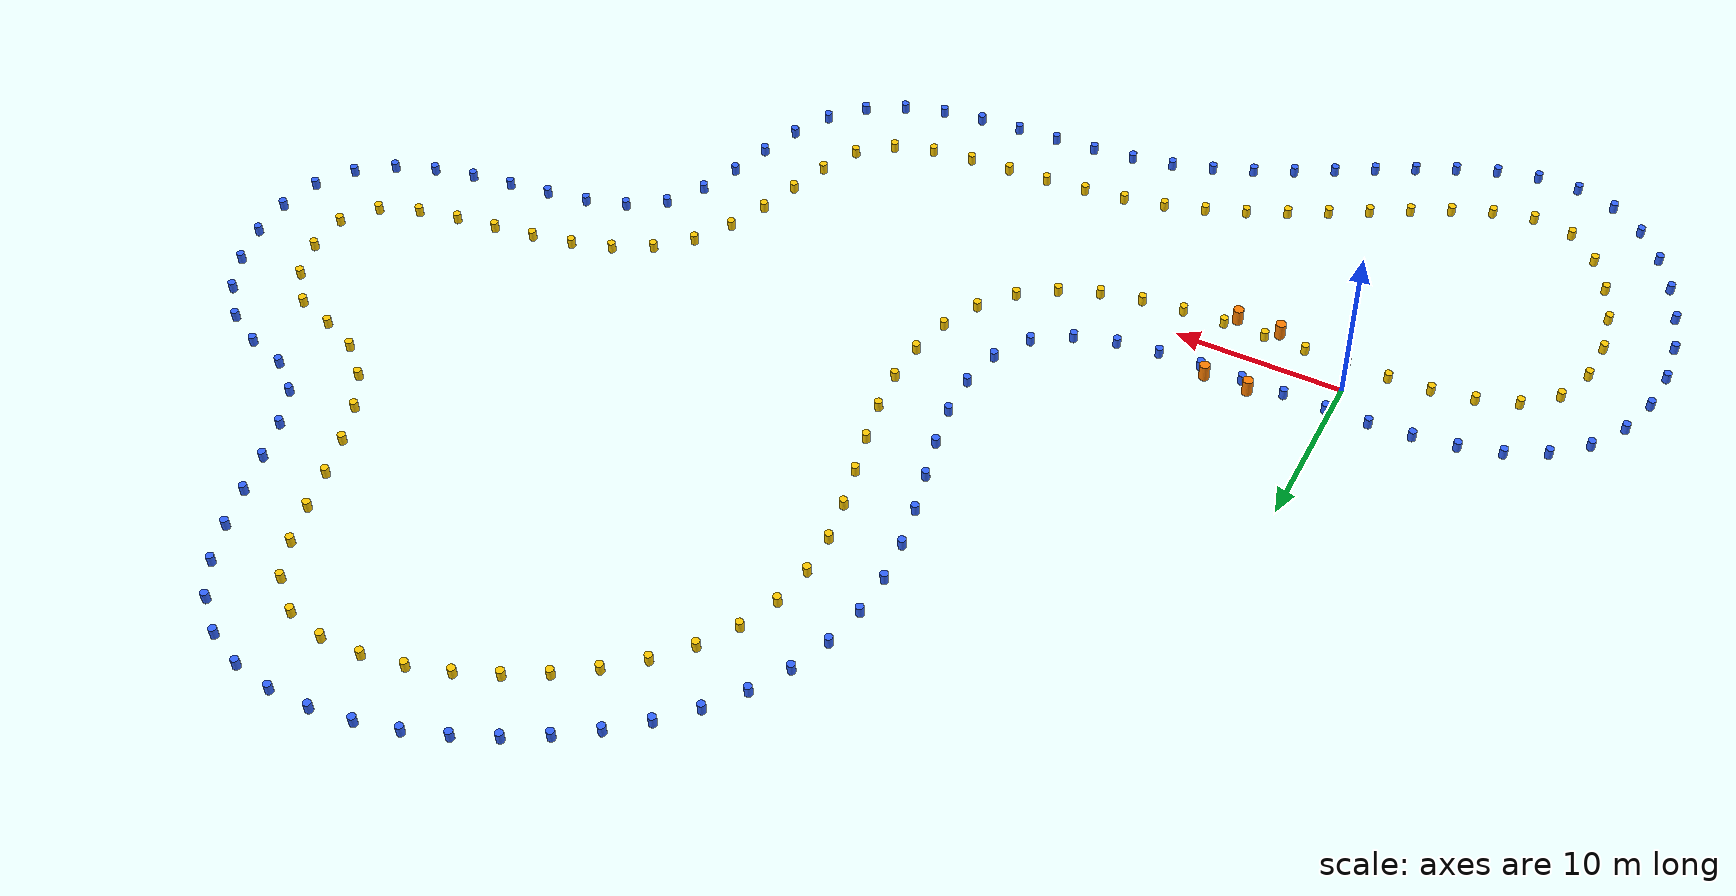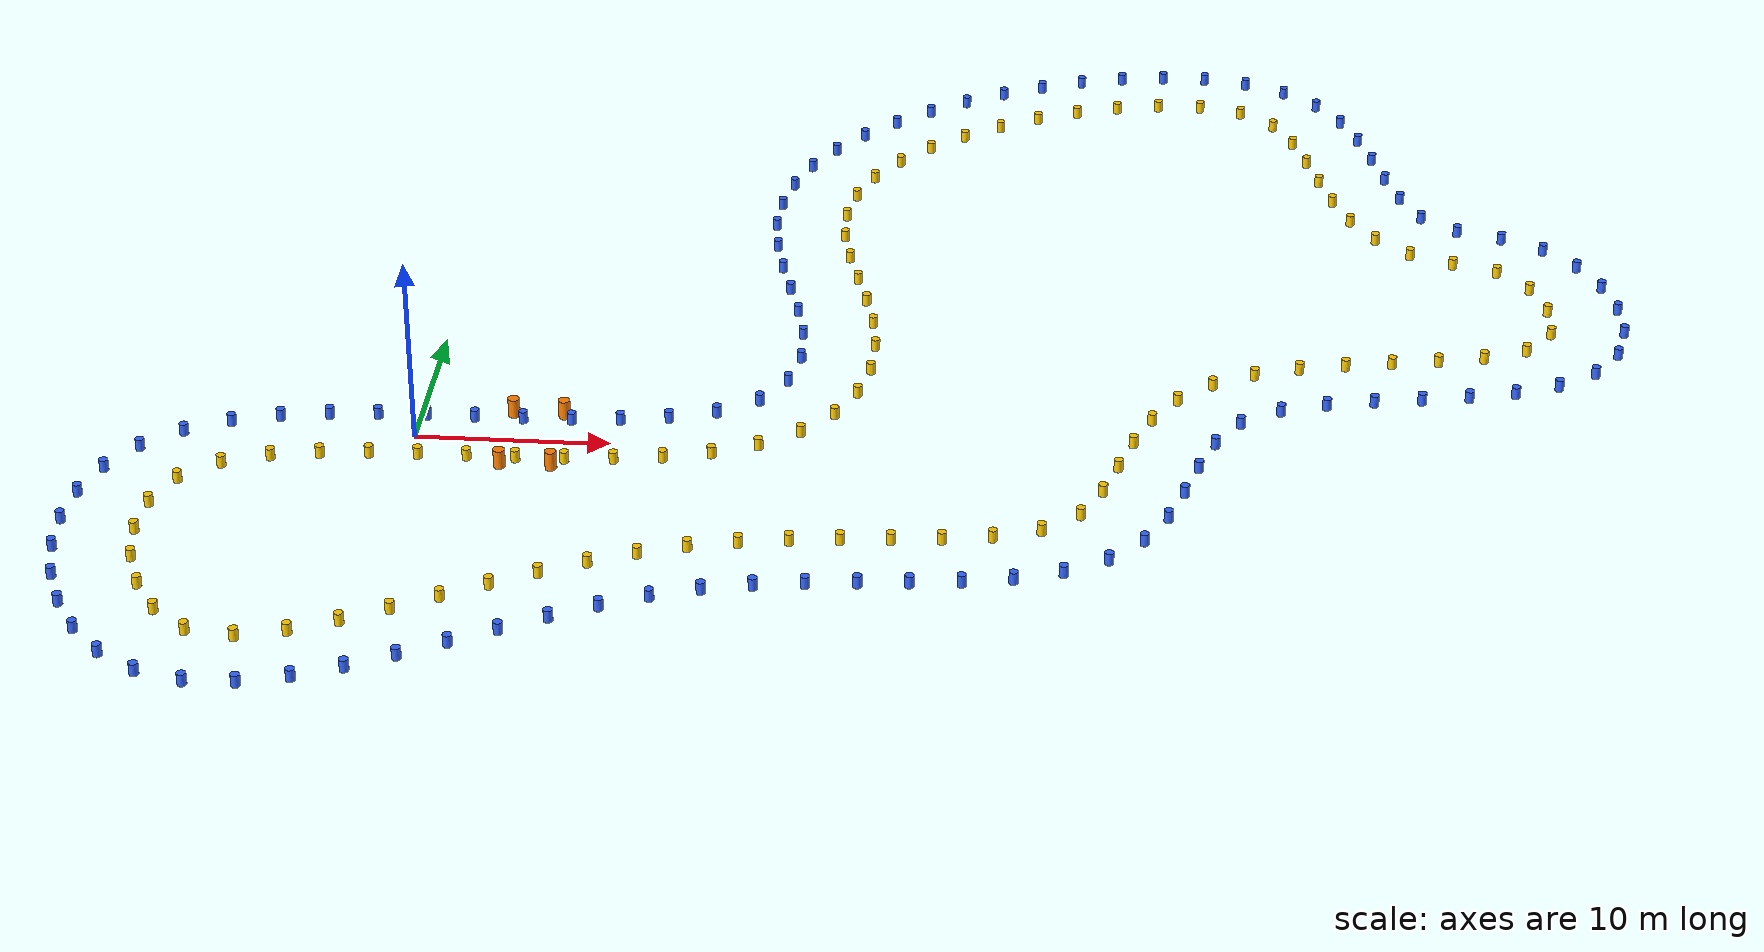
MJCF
<?xml version="1.0" ?>
<mujoco model="random_track">
  <compiler angle="radian" coordinate="local" autolimits="true"/>
  <default>
    <default class="cone">
      <joint type="free" damping="0.1" frictionloss="0.05"/>
      <geom condim="4" friction="0.5 0.005 0.0001" solref="0.02 1.0" solimp="0.99 0.99 0.001"/>
    </default>
  </default>
  <asset>
    <material name="blue_cone" rgba="0.2 0.4 1.0 1.0" specular="0.5" shininess="0.2"/>
    <material name="yellow_cone" rgba="1.0 0.8 0.0 1.0" specular="0.5" shininess="0.2"/>
    <material name="orange_cone" rgba="1.0 0.5 0.0 1.0" specular="0.5" shininess="0.2"/>
  </asset>
  <worldbody>
    <body name="cone_left_0000" pos="37.01535454981153 -7.561578160280675 0.325">
      <joint name="cone_left_joint_0000" type="free" damping="0.1" frictionloss="0.05"/>
      <geom name="cone_left_vis_0000" type="cylinder" size="0.228 0.325" material="blue_cone" mass="1.0" density="100" condim="4" friction="0.5 0.005 0.0001" solref="0.02 1.0" solimp="0.99 0.99 0.001"/>
    </body>
    <body name="cone_left_0001" pos="35.31192166856074 -9.363468383609785 0.325">
      <joint name="cone_left_joint_0001" type="free" damping="0.1" frictionloss="0.05"/>
      <geom name="cone_left_vis_0001" type="cylinder" size="0.228 0.325" material="blue_cone" mass="1.0" density="100" condim="4" friction="0.5 0.005 0.0001" solref="0.02 1.0" solimp="0.99 0.99 0.001"/>
    </body>
    <body name="cone_left_0002" pos="33.163749354223604 -10.607460300066588 0.325">
      <joint name="cone_left_joint_0002" type="free" damping="0.1" frictionloss="0.05"/>
      <geom name="cone_left_vis_0002" type="cylinder" size="0.228 0.325" material="blue_cone" mass="1.0" density="100" condim="4" friction="0.5 0.005 0.0001" solref="0.02 1.0" solimp="0.99 0.99 0.001"/>
    </body>
    <body name="cone_left_0003" pos="30.79154000437468 -11.351767163467596 0.325">
      <joint name="cone_left_joint_0003" type="free" damping="0.1" frictionloss="0.05"/>
      <geom name="cone_left_vis_0003" type="cylinder" size="0.228 0.325" material="blue_cone" mass="1.0" density="100" condim="4" friction="0.5 0.005 0.0001" solref="0.02 1.0" solimp="0.99 0.99 0.001"/>
    </body>
    <body name="cone_left_0004" pos="28.33714438596126 -11.762268319283574 0.325">
      <joint name="cone_left_joint_0004" type="free" damping="0.1" frictionloss="0.05"/>
      <geom name="cone_left_vis_0004" type="cylinder" size="0.228 0.325" material="blue_cone" mass="1.0" density="100" condim="4" friction="0.5 0.005 0.0001" solref="0.02 1.0" solimp="0.99 0.99 0.001"/>
    </body>
    <body name="cone_left_0005" pos="25.85867578710478 -11.99481565442457 0.325">
      <joint name="cone_left_joint_0005" type="free" damping="0.1" frictionloss="0.05"/>
      <geom name="cone_left_vis_0005" type="cylinder" size="0.228 0.325" material="blue_cone" mass="1.0" density="100" condim="4" friction="0.5 0.005 0.0001" solref="0.02 1.0" solimp="0.99 0.99 0.001"/>
    </body>
    <body name="cone_left_0006" pos="23.37507821105306 -12.167170132034908 0.325">
      <joint name="cone_left_joint_0006" type="free" damping="0.1" frictionloss="0.05"/>
      <geom name="cone_left_vis_0006" type="cylinder" size="0.228 0.325" material="blue_cone" mass="1.0" density="100" condim="4" friction="0.5 0.005 0.0001" solref="0.02 1.0" solimp="0.99 0.99 0.001"/>
    </body>
    <body name="cone_left_0007" pos="20.894013253403344 -12.371684172666768 0.325">
      <joint name="cone_left_joint_0007" type="free" damping="0.1" frictionloss="0.05"/>
      <geom name="cone_left_vis_0007" type="cylinder" size="0.228 0.325" material="blue_cone" mass="1.0" density="100" condim="4" friction="0.5 0.005 0.0001" solref="0.02 1.0" solimp="0.99 0.99 0.001"/>
    </body>
    <body name="cone_left_0008" pos="18.42530151325319 -12.690113060591084 0.325">
      <joint name="cone_left_joint_0008" type="free" damping="0.1" frictionloss="0.05"/>
      <geom name="cone_left_vis_0008" type="cylinder" size="0.228 0.325" material="blue_cone" mass="1.0" density="100" condim="4" friction="0.5 0.005 0.0001" solref="0.02 1.0" solimp="0.99 0.99 0.001"/>
    </body>
    <body name="cone_left_0009" pos="15.990251383898546 -13.20354108529964 0.325">
      <joint name="cone_left_joint_0009" type="free" damping="0.1" frictionloss="0.05"/>
      <geom name="cone_left_vis_0009" type="cylinder" size="0.228 0.325" material="blue_cone" mass="1.0" density="100" condim="4" friction="0.5 0.005 0.0001" solref="0.02 1.0" solimp="0.99 0.99 0.001"/>
    </body>
    <body name="cone_left_0010" pos="13.62210810851364 -13.968114073621809 0.325">
      <joint name="cone_left_joint_0010" type="free" damping="0.1" frictionloss="0.05"/>
      <geom name="cone_left_vis_0010" type="cylinder" size="0.228 0.325" material="blue_cone" mass="1.0" density="100" condim="4" friction="0.5 0.005 0.0001" solref="0.02 1.0" solimp="0.99 0.99 0.001"/>
    </body>
    <body name="cone_left_0011" pos="11.327423894426847 -14.93234352316496 0.325">
      <joint name="cone_left_joint_0011" type="free" damping="0.1" frictionloss="0.05"/>
      <geom name="cone_left_vis_0011" type="cylinder" size="0.228 0.325" material="blue_cone" mass="1.0" density="100" condim="4" friction="0.5 0.005 0.0001" solref="0.02 1.0" solimp="0.99 0.99 0.001"/>
    </body>
    <body name="cone_left_0012" pos="9.09283032806549 -16.029353997895473 0.325">
      <joint name="cone_left_joint_0012" type="free" damping="0.1" frictionloss="0.05"/>
      <geom name="cone_left_vis_0012" type="cylinder" size="0.228 0.325" material="blue_cone" mass="1.0" density="100" condim="4" friction="0.5 0.005 0.0001" solref="0.02 1.0" solimp="0.99 0.99 0.001"/>
    </body>
    <body name="cone_left_0013" pos="6.898429659629554 -17.205051579126042 0.325">
      <joint name="cone_left_joint_0013" type="free" damping="0.1" frictionloss="0.05"/>
      <geom name="cone_left_vis_0013" type="cylinder" size="0.228 0.325" material="blue_cone" mass="1.0" density="100" condim="4" friction="0.5 0.005 0.0001" solref="0.02 1.0" solimp="0.99 0.99 0.001"/>
    </body>
    <body name="cone_left_0014" pos="4.7206804218565726 -18.411444214252178 0.325">
      <joint name="cone_left_joint_0014" type="free" damping="0.1" frictionloss="0.05"/>
      <geom name="cone_left_vis_0014" type="cylinder" size="0.228 0.325" material="blue_cone" mass="1.0" density="100" condim="4" friction="0.5 0.005 0.0001" solref="0.02 1.0" solimp="0.99 0.99 0.001"/>
    </body>
    <body name="cone_left_0015" pos="2.5324129208698514 -19.598551175331984 0.325">
      <joint name="cone_left_joint_0015" type="free" damping="0.1" frictionloss="0.05"/>
      <geom name="cone_left_vis_0015" type="cylinder" size="0.228 0.325" material="blue_cone" mass="1.0" density="100" condim="4" friction="0.5 0.005 0.0001" solref="0.02 1.0" solimp="0.99 0.99 0.001"/>
    </body>
    <body name="cone_left_0016" pos="0.3019859936175582 -20.703832379391514 0.325">
      <joint name="cone_left_joint_0016" type="free" damping="0.1" frictionloss="0.05"/>
      <geom name="cone_left_vis_0016" type="cylinder" size="0.228 0.325" material="blue_cone" mass="1.0" density="100" condim="4" friction="0.5 0.005 0.0001" solref="0.02 1.0" solimp="0.99 0.99 0.001"/>
    </body>
    <body name="cone_left_0017" pos="-2.0056543325420293 -21.635137850553694 0.325">
      <joint name="cone_left_joint_0017" type="free" damping="0.1" frictionloss="0.05"/>
      <geom name="cone_left_vis_0017" type="cylinder" size="0.228 0.325" material="blue_cone" mass="1.0" density="100" condim="4" friction="0.5 0.005 0.0001" solref="0.02 1.0" solimp="0.99 0.99 0.001"/>
    </body>
    <body name="cone_left_0018" pos="-4.416169405093465 -22.244777261399072 0.325">
      <joint name="cone_left_joint_0018" type="free" damping="0.1" frictionloss="0.05"/>
      <geom name="cone_left_vis_0018" type="cylinder" size="0.228 0.325" material="blue_cone" mass="1.0" density="100" condim="4" friction="0.5 0.005 0.0001" solref="0.02 1.0" solimp="0.99 0.99 0.001"/>
    </body>
    <body name="cone_left_0019" pos="-6.897410639753637 -22.315180360973052 0.325">
      <joint name="cone_left_joint_0019" type="free" damping="0.1" frictionloss="0.05"/>
      <geom name="cone_left_vis_0019" type="cylinder" size="0.228 0.325" material="blue_cone" mass="1.0" density="100" condim="4" friction="0.5 0.005 0.0001" solref="0.02 1.0" solimp="0.99 0.99 0.001"/>
    </body>
    <body name="cone_left_0020" pos="-9.284006511028847 -21.647154598045642 0.325">
      <joint name="cone_left_joint_0020" type="free" damping="0.1" frictionloss="0.05"/>
      <geom name="cone_left_vis_0020" type="cylinder" size="0.228 0.325" material="blue_cone" mass="1.0" density="100" condim="4" friction="0.5 0.005 0.0001" solref="0.02 1.0" solimp="0.99 0.99 0.001"/>
    </body>
    <body name="cone_left_0021" pos="-11.335930647627185 -20.254492972240627 0.325">
      <joint name="cone_left_joint_0021" type="free" damping="0.1" frictionloss="0.05"/>
      <geom name="cone_left_vis_0021" type="cylinder" size="0.228 0.325" material="blue_cone" mass="1.0" density="100" condim="4" friction="0.5 0.005 0.0001" solref="0.02 1.0" solimp="0.99 0.99 0.001"/>
    </body>
    <body name="cone_left_0022" pos="-12.966805581465144 -18.379739317251083 0.325">
      <joint name="cone_left_joint_0022" type="free" damping="0.1" frictionloss="0.05"/>
      <geom name="cone_left_vis_0022" type="cylinder" size="0.228 0.325" material="blue_cone" mass="1.0" density="100" condim="4" friction="0.5 0.005 0.0001" solref="0.02 1.0" solimp="0.99 0.99 0.001"/>
    </body>
    <body name="cone_left_0023" pos="-14.225485595521105 -16.23494362213882 0.325">
      <joint name="cone_left_joint_0023" type="free" damping="0.1" frictionloss="0.05"/>
      <geom name="cone_left_vis_0023" type="cylinder" size="0.228 0.325" material="blue_cone" mass="1.0" density="100" condim="4" friction="0.5 0.005 0.0001" solref="0.02 1.0" solimp="0.99 0.99 0.001"/>
    </body>
    <body name="cone_left_0024" pos="-15.147879949615346 -13.924835661663462 0.325">
      <joint name="cone_left_joint_0024" type="free" damping="0.1" frictionloss="0.05"/>
      <geom name="cone_left_vis_0024" type="cylinder" size="0.228 0.325" material="blue_cone" mass="1.0" density="100" condim="4" friction="0.5 0.005 0.0001" solref="0.02 1.0" solimp="0.99 0.99 0.001"/>
    </body>
    <body name="cone_left_0025" pos="-15.73440409485964 -11.507572530324211 0.325">
      <joint name="cone_left_joint_0025" type="free" damping="0.1" frictionloss="0.05"/>
      <geom name="cone_left_vis_0025" type="cylinder" size="0.228 0.325" material="blue_cone" mass="1.0" density="100" condim="4" friction="0.5 0.005 0.0001" solref="0.02 1.0" solimp="0.99 0.99 0.001"/>
    </body>
    <body name="cone_left_0026" pos="-15.949681040800117 -9.03006863191753 0.325">
      <joint name="cone_left_joint_0026" type="free" damping="0.1" frictionloss="0.05"/>
      <geom name="cone_left_vis_0026" type="cylinder" size="0.228 0.325" material="blue_cone" mass="1.0" density="100" condim="4" friction="0.5 0.005 0.0001" solref="0.02 1.0" solimp="0.99 0.99 0.001"/>
    </body>
    <body name="cone_left_0027" pos="-15.723950017755621 -6.55470091344921 0.325">
      <joint name="cone_left_joint_0027" type="free" damping="0.1" frictionloss="0.05"/>
      <geom name="cone_left_vis_0027" type="cylinder" size="0.228 0.325" material="blue_cone" mass="1.0" density="100" condim="4" friction="0.5 0.005 0.0001" solref="0.02 1.0" solimp="0.99 0.99 0.001"/>
    </body>
    <body name="cone_left_0028" pos="-14.981444670564882 -4.184403502309408 0.325">
      <joint name="cone_left_joint_0028" type="free" damping="0.1" frictionloss="0.05"/>
      <geom name="cone_left_vis_0028" type="cylinder" size="0.228 0.325" material="blue_cone" mass="1.0" density="100" condim="4" friction="0.5 0.005 0.0001" solref="0.02 1.0" solimp="0.99 0.99 0.001"/>
    </body>
    <body name="cone_left_0029" pos="-13.646628620971226 -2.0934533518813367 0.325">
      <joint name="cone_left_joint_0029" type="free" damping="0.1" frictionloss="0.05"/>
      <geom name="cone_left_vis_0029" type="cylinder" size="0.228 0.325" material="blue_cone" mass="1.0" density="100" condim="4" friction="0.5 0.005 0.0001" solref="0.02 1.0" solimp="0.99 0.99 0.001"/>
    </body>
    <body name="cone_left_0030" pos="-11.768815978739687 -0.47150359567680056 0.325">
      <joint name="cone_left_joint_0030" type="free" damping="0.1" frictionloss="0.05"/>
      <geom name="cone_left_vis_0030" type="cylinder" size="0.228 0.325" material="blue_cone" mass="1.0" density="100" condim="4" friction="0.5 0.005 0.0001" solref="0.02 1.0" solimp="0.99 0.99 0.001"/>
    </body>
    <body name="cone_left_0031" pos="-9.542179707777612 0.6306530655580929 0.325">
      <joint name="cone_left_joint_0031" type="free" damping="0.1" frictionloss="0.05"/>
      <geom name="cone_left_vis_0031" type="cylinder" size="0.228 0.325" material="blue_cone" mass="1.0" density="100" condim="4" friction="0.5 0.005 0.0001" solref="0.02 1.0" solimp="0.99 0.99 0.001"/>
    </body>
    <body name="cone_left_0032" pos="-7.147307622447604 1.3018785700704854 0.325">
      <joint name="cone_left_joint_0032" type="free" damping="0.1" frictionloss="0.05"/>
      <geom name="cone_left_vis_0032" type="cylinder" size="0.228 0.325" material="blue_cone" mass="1.0" density="100" condim="4" friction="0.5 0.005 0.0001" solref="0.02 1.0" solimp="0.99 0.99 0.001"/>
    </body>
    <body name="cone_left_0033" pos="-4.686343614231641 1.6713903403382702 0.325">
      <joint name="cone_left_joint_0033" type="free" damping="0.1" frictionloss="0.05"/>
      <geom name="cone_left_vis_0033" type="cylinder" size="0.228 0.325" material="blue_cone" mass="1.0" density="100" condim="4" friction="0.5 0.005 0.0001" solref="0.02 1.0" solimp="0.99 0.99 0.001"/>
    </body>
    <body name="cone_left_0034" pos="-2.2032606836122497 1.8455618971920842 0.325">
      <joint name="cone_left_joint_0034" type="free" damping="0.1" frictionloss="0.05"/>
      <geom name="cone_left_vis_0034" type="cylinder" size="0.228 0.325" material="blue_cone" mass="1.0" density="100" condim="4" friction="0.5 0.005 0.0001" solref="0.02 1.0" solimp="0.99 0.99 0.001"/>
    </body>
    <body name="cone_left_0035" pos="0.2855361160894212 1.9027192870101217 0.325">
      <joint name="cone_left_joint_0035" type="free" damping="0.1" frictionloss="0.05"/>
      <geom name="cone_left_vis_0035" type="cylinder" size="0.228 0.325" material="blue_cone" mass="1.0" density="100" condim="4" friction="0.5 0.005 0.0001" solref="0.02 1.0" solimp="0.99 0.99 0.001"/>
    </body>
    <body name="cone_left_0036" pos="2.7750940269267383 1.9025632748722217 0.325">
      <joint name="cone_left_joint_0036" type="free" damping="0.1" frictionloss="0.05"/>
      <geom name="cone_left_vis_0036" type="cylinder" size="0.228 0.325" material="blue_cone" mass="1.0" density="100" condim="4" friction="0.5 0.005 0.0001" solref="0.02 1.0" solimp="0.99 0.99 0.001"/>
    </body>
    <body name="cone_left_0037" pos="5.2646540004014515 1.895958994388259 0.325">
      <joint name="cone_left_joint_0037" type="free" damping="0.1" frictionloss="0.05"/>
      <geom name="cone_left_vis_0037" type="cylinder" size="0.228 0.325" material="blue_cone" mass="1.0" density="100" condim="4" friction="0.5 0.005 0.0001" solref="0.02 1.0" solimp="0.99 0.99 0.001"/>
    </body>
    <body name="cone_left_0038" pos="7.753842105178184 1.934376248433182 0.325">
      <joint name="cone_left_joint_0038" type="free" damping="0.1" frictionloss="0.05"/>
      <geom name="cone_left_vis_0038" type="cylinder" size="0.228 0.325" material="blue_cone" mass="1.0" density="100" condim="4" friction="0.5 0.005 0.0001" solref="0.02 1.0" solimp="0.99 0.99 0.001"/>
    </body>
    <body name="cone_left_0039" pos="10.23871311866277 2.081239497920542 0.325">
      <joint name="cone_left_joint_0039" type="free" damping="0.1" frictionloss="0.05"/>
      <geom name="cone_left_vis_0039" type="cylinder" size="0.228 0.325" material="blue_cone" mass="1.0" density="100" condim="4" friction="0.5 0.005 0.0001" solref="0.02 1.0" solimp="0.99 0.99 0.001"/>
    </body>
    <body name="cone_left_0040" pos="12.702640031058905 2.4291276814220026 0.325">
      <joint name="cone_left_joint_0040" type="free" damping="0.1" frictionloss="0.05"/>
      <geom name="cone_left_vis_0040" type="cylinder" size="0.228 0.325" material="blue_cone" mass="1.0" density="100" condim="4" friction="0.5 0.005 0.0001" solref="0.02 1.0" solimp="0.99 0.99 0.001"/>
    </body>
    <body name="cone_left_0041" pos="15.084797978523532 3.1380327527200933 0.325">
      <joint name="cone_left_joint_0041" type="free" damping="0.1" frictionloss="0.05"/>
      <geom name="cone_left_vis_0041" type="cylinder" size="0.228 0.325" material="blue_cone" mass="1.0" density="100" condim="4" friction="0.5 0.005 0.0001" solref="0.02 1.0" solimp="0.99 0.99 0.001"/>
    </body>
    <body name="cone_left_0042" pos="17.162566968670006 4.481711743314243 0.325">
      <joint name="cone_left_joint_0042" type="free" damping="0.1" frictionloss="0.05"/>
      <geom name="cone_left_vis_0042" type="cylinder" size="0.228 0.325" material="blue_cone" mass="1.0" density="100" condim="4" friction="0.5 0.005 0.0001" solref="0.02 1.0" solimp="0.99 0.99 0.001"/>
    </body>
    <body name="cone_left_0043" pos="18.453537730977217 6.58505417381528 0.325">
      <joint name="cone_left_joint_0043" type="free" damping="0.1" frictionloss="0.05"/>
      <geom name="cone_left_vis_0043" type="cylinder" size="0.228 0.325" material="blue_cone" mass="1.0" density="100" condim="4" friction="0.5 0.005 0.0001" solref="0.02 1.0" solimp="0.99 0.99 0.001"/>
    </body>
    <body name="cone_left_0044" pos="18.93387473493066 9.019324676307491 0.325">
      <joint name="cone_left_joint_0044" type="free" damping="0.1" frictionloss="0.05"/>
      <geom name="cone_left_vis_0044" type="cylinder" size="0.228 0.325" material="blue_cone" mass="1.0" density="100" condim="4" friction="0.5 0.005 0.0001" solref="0.02 1.0" solimp="0.99 0.99 0.001"/>
    </body>
    <body name="cone_left_0045" pos="18.822332261381447 11.50256119796365 0.325">
      <joint name="cone_left_joint_0045" type="free" damping="0.1" frictionloss="0.05"/>
      <geom name="cone_left_vis_0045" type="cylinder" size="0.228 0.325" material="blue_cone" mass="1.0" density="100" condim="4" friction="0.5 0.005 0.0001" solref="0.02 1.0" solimp="0.99 0.99 0.001"/>
    </body>
    <body name="cone_left_0046" pos="18.357798947794272 13.947378267482748 0.325">
      <joint name="cone_left_joint_0046" type="free" damping="0.1" frictionloss="0.05"/>
      <geom name="cone_left_vis_0046" type="cylinder" size="0.228 0.325" material="blue_cone" mass="1.0" density="100" condim="4" friction="0.5 0.005 0.0001" solref="0.02 1.0" solimp="0.99 0.99 0.001"/>
    </body>
    <body name="cone_left_0047" pos="17.740483651125395 16.359102374844355 0.325">
      <joint name="cone_left_joint_0047" type="free" damping="0.1" frictionloss="0.05"/>
      <geom name="cone_left_vis_0047" type="cylinder" size="0.228 0.325" material="blue_cone" mass="1.0" density="100" condim="4" friction="0.5 0.005 0.0001" solref="0.02 1.0" solimp="0.99 0.99 0.001"/>
    </body>
    <body name="cone_left_0048" pos="17.117607356825822 18.76942951458014 0.325">
      <joint name="cone_left_joint_0048" type="free" damping="0.1" frictionloss="0.05"/>
      <geom name="cone_left_vis_0048" type="cylinder" size="0.228 0.325" material="blue_cone" mass="1.0" density="100" condim="4" friction="0.5 0.005 0.0001" solref="0.02 1.0" solimp="0.99 0.99 0.001"/>
    </body>
    <body name="cone_left_0049" pos="16.614638985191974 21.207069492876023 0.325">
      <joint name="cone_left_joint_0049" type="free" damping="0.1" frictionloss="0.05"/>
      <geom name="cone_left_vis_0049" type="cylinder" size="0.228 0.325" material="blue_cone" mass="1.0" density="100" condim="4" friction="0.5 0.005 0.0001" solref="0.02 1.0" solimp="0.99 0.99 0.001"/>
    </body>
    <body name="cone_left_0050" pos="16.3559063586902 23.681545596655745 0.325">
      <joint name="cone_left_joint_0050" type="free" damping="0.1" frictionloss="0.05"/>
      <geom name="cone_left_vis_0050" type="cylinder" size="0.228 0.325" material="blue_cone" mass="1.0" density="100" condim="4" friction="0.5 0.005 0.0001" solref="0.02 1.0" solimp="0.99 0.99 0.001"/>
    </body>
    <body name="cone_left_0051" pos="16.4411039239182 26.167364212883776 0.325">
      <joint name="cone_left_joint_0051" type="free" damping="0.1" frictionloss="0.05"/>
      <geom name="cone_left_vis_0051" type="cylinder" size="0.228 0.325" material="blue_cone" mass="1.0" density="100" condim="4" friction="0.5 0.005 0.0001" solref="0.02 1.0" solimp="0.99 0.99 0.001"/>
    </body>
    <body name="cone_left_0052" pos="16.90709735572837 28.610281329699056 0.325">
      <joint name="cone_left_joint_0052" type="free" damping="0.1" frictionloss="0.05"/>
      <geom name="cone_left_vis_0052" type="cylinder" size="0.228 0.325" material="blue_cone" mass="1.0" density="100" condim="4" friction="0.5 0.005 0.0001" solref="0.02 1.0" solimp="0.99 0.99 0.001"/>
    </body>
    <body name="cone_left_0053" pos="17.759801043233807 30.94636388295941 0.325">
      <joint name="cone_left_joint_0053" type="free" damping="0.1" frictionloss="0.05"/>
      <geom name="cone_left_vis_0053" type="cylinder" size="0.228 0.325" material="blue_cone" mass="1.0" density="100" condim="4" friction="0.5 0.005 0.0001" solref="0.02 1.0" solimp="0.99 0.99 0.001"/>
    </body>
    <body name="cone_left_0054" pos="18.976195580225813 33.11556353448017 0.325">
      <joint name="cone_left_joint_0054" type="free" damping="0.1" frictionloss="0.05"/>
      <geom name="cone_left_vis_0054" type="cylinder" size="0.228 0.325" material="blue_cone" mass="1.0" density="100" condim="4" friction="0.5 0.005 0.0001" solref="0.02 1.0" solimp="0.99 0.99 0.001"/>
    </body>
    <body name="cone_left_0055" pos="20.496932298437876 35.08432227810167 0.325">
      <joint name="cone_left_joint_0055" type="free" damping="0.1" frictionloss="0.05"/>
      <geom name="cone_left_vis_0055" type="cylinder" size="0.228 0.325" material="blue_cone" mass="1.0" density="100" condim="4" friction="0.5 0.005 0.0001" solref="0.02 1.0" solimp="0.99 0.99 0.001"/>
    </body>
    <body name="cone_left_0056" pos="22.244732809066477 36.85542756465957 0.325">
      <joint name="cone_left_joint_0056" type="free" damping="0.1" frictionloss="0.05"/>
      <geom name="cone_left_vis_0056" type="cylinder" size="0.228 0.325" material="blue_cone" mass="1.0" density="100" condim="4" friction="0.5 0.005 0.0001" solref="0.02 1.0" solimp="0.99 0.99 0.001"/>
    </body>
    <body name="cone_left_0057" pos="24.164258338459813 38.43929445221658 0.325">
      <joint name="cone_left_joint_0057" type="free" damping="0.1" frictionloss="0.05"/>
      <geom name="cone_left_vis_0057" type="cylinder" size="0.228 0.325" material="blue_cone" mass="1.0" density="100" condim="4" friction="0.5 0.005 0.0001" solref="0.02 1.0" solimp="0.99 0.99 0.001"/>
    </body>
    <body name="cone_left_0058" pos="26.219123483656844 39.843420594947126 0.325">
      <joint name="cone_left_joint_0058" type="free" damping="0.1" frictionloss="0.05"/>
      <geom name="cone_left_vis_0058" type="cylinder" size="0.228 0.325" material="blue_cone" mass="1.0" density="100" condim="4" friction="0.5 0.005 0.0001" solref="0.02 1.0" solimp="0.99 0.99 0.001"/>
    </body>
    <body name="cone_left_0059" pos="28.385415947748776 41.06880268249164 0.325">
      <joint name="cone_left_joint_0059" type="free" damping="0.1" frictionloss="0.05"/>
      <geom name="cone_left_vis_0059" type="cylinder" size="0.228 0.325" material="blue_cone" mass="1.0" density="100" condim="4" friction="0.5 0.005 0.0001" solref="0.02 1.0" solimp="0.99 0.99 0.001"/>
    </body>
    <body name="cone_left_0060" pos="30.646671598712715 42.108491913597994 0.325">
      <joint name="cone_left_joint_0060" type="free" damping="0.1" frictionloss="0.05"/>
      <geom name="cone_left_vis_0060" type="cylinder" size="0.228 0.325" material="blue_cone" mass="1.0" density="100" condim="4" friction="0.5 0.005 0.0001" solref="0.02 1.0" solimp="0.99 0.99 0.001"/>
    </body>
    <body name="cone_left_0061" pos="32.990133262463246 42.94620310965363 0.325">
      <joint name="cone_left_joint_0061" type="free" damping="0.1" frictionloss="0.05"/>
      <geom name="cone_left_vis_0061" type="cylinder" size="0.228 0.325" material="blue_cone" mass="1.0" density="100" condim="4" friction="0.5 0.005 0.0001" solref="0.02 1.0" solimp="0.99 0.99 0.001"/>
    </body>
    <body name="cone_left_0062" pos="35.403739668563865 43.551778670088375 0.325">
      <joint name="cone_left_joint_0062" type="free" damping="0.1" frictionloss="0.05"/>
      <geom name="cone_left_vis_0062" type="cylinder" size="0.228 0.325" material="blue_cone" mass="1.0" density="100" condim="4" friction="0.5 0.005 0.0001" solref="0.02 1.0" solimp="0.99 0.99 0.001"/>
    </body>
    <body name="cone_left_0063" pos="37.87031423332901 43.876808681850726 0.325">
      <joint name="cone_left_joint_0063" type="free" damping="0.1" frictionloss="0.05"/>
      <geom name="cone_left_vis_0063" type="cylinder" size="0.228 0.325" material="blue_cone" mass="1.0" density="100" condim="4" friction="0.5 0.005 0.0001" solref="0.02 1.0" solimp="0.99 0.99 0.001"/>
    </body>
    <body name="cone_left_0064" pos="40.356981987720864 43.84625995371055 0.325">
      <joint name="cone_left_joint_0064" type="free" damping="0.1" frictionloss="0.05"/>
      <geom name="cone_left_vis_0064" type="cylinder" size="0.228 0.325" material="blue_cone" mass="1.0" density="100" condim="4" friction="0.5 0.005 0.0001" solref="0.02 1.0" solimp="0.99 0.99 0.001"/>
    </body>
    <body name="cone_left_0065" pos="42.793882217043226 43.36004228137214 0.325">
      <joint name="cone_left_joint_0065" type="free" damping="0.1" frictionloss="0.05"/>
      <geom name="cone_left_vis_0065" type="cylinder" size="0.228 0.325" material="blue_cone" mass="1.0" density="100" condim="4" friction="0.5 0.005 0.0001" solref="0.02 1.0" solimp="0.99 0.99 0.001"/>
    </body>
    <body name="cone_left_0066" pos="45.04553249531752 42.31527267520155 0.325">
      <joint name="cone_left_joint_0066" type="free" damping="0.1" frictionloss="0.05"/>
      <geom name="cone_left_vis_0066" type="cylinder" size="0.228 0.325" material="blue_cone" mass="1.0" density="100" condim="4" friction="0.5 0.005 0.0001" solref="0.02 1.0" solimp="0.99 0.99 0.001"/>
    </body>
    <body name="cone_left_0067" pos="46.91297695530096 40.68301198805508 0.325">
      <joint name="cone_left_joint_0067" type="free" damping="0.1" frictionloss="0.05"/>
      <geom name="cone_left_vis_0067" type="cylinder" size="0.228 0.325" material="blue_cone" mass="1.0" density="100" condim="4" friction="0.5 0.005 0.0001" solref="0.02 1.0" solimp="0.99 0.99 0.001"/>
    </body>
    <body name="cone_left_0068" pos="48.25629369977961 38.594403517845045 0.325">
      <joint name="cone_left_joint_0068" type="free" damping="0.1" frictionloss="0.05"/>
      <geom name="cone_left_vis_0068" type="cylinder" size="0.228 0.325" material="blue_cone" mass="1.0" density="100" condim="4" friction="0.5 0.005 0.0001" solref="0.02 1.0" solimp="0.99 0.99 0.001"/>
    </body>
    <body name="cone_left_0069" pos="49.18296364880671 36.28591076509462 0.325">
      <joint name="cone_left_joint_0069" type="free" damping="0.1" frictionloss="0.05"/>
      <geom name="cone_left_vis_0069" type="cylinder" size="0.228 0.325" material="blue_cone" mass="1.0" density="100" condim="4" friction="0.5 0.005 0.0001" solref="0.02 1.0" solimp="0.99 0.99 0.001"/>
    </body>
    <body name="cone_left_0070" pos="49.88009147950109 33.896338082385064 0.325">
      <joint name="cone_left_joint_0070" type="free" damping="0.1" frictionloss="0.05"/>
      <geom name="cone_left_vis_0070" type="cylinder" size="0.228 0.325" material="blue_cone" mass="1.0" density="100" condim="4" friction="0.5 0.005 0.0001" solref="0.02 1.0" solimp="0.99 0.99 0.001"/>
    </body>
    <body name="cone_left_0071" pos="50.50995792315864 31.487768520633615 0.325">
      <joint name="cone_left_joint_0071" type="free" damping="0.1" frictionloss="0.05"/>
      <geom name="cone_left_vis_0071" type="cylinder" size="0.228 0.325" material="blue_cone" mass="1.0" density="100" condim="4" friction="0.5 0.005 0.0001" solref="0.02 1.0" solimp="0.99 0.99 0.001"/>
    </body>
    <body name="cone_left_0072" pos="51.235935501736854 29.10713672564797 0.325">
      <joint name="cone_left_joint_0072" type="free" damping="0.1" frictionloss="0.05"/>
      <geom name="cone_left_vis_0072" type="cylinder" size="0.228 0.325" material="blue_cone" mass="1.0" density="100" condim="4" friction="0.5 0.005 0.0001" solref="0.02 1.0" solimp="0.99 0.99 0.001"/>
    </body>
    <body name="cone_left_0073" pos="52.31334956898101 26.869937315449924 0.325">
      <joint name="cone_left_joint_0073" type="free" damping="0.1" frictionloss="0.05"/>
      <geom name="cone_left_vis_0073" type="cylinder" size="0.228 0.325" material="blue_cone" mass="1.0" density="100" condim="4" friction="0.5 0.005 0.0001" solref="0.02 1.0" solimp="0.99 0.99 0.001"/>
    </body>
    <body name="cone_left_0074" pos="54.22380662414948 25.350557688033724 0.325">
      <joint name="cone_left_joint_0074" type="free" damping="0.1" frictionloss="0.05"/>
      <geom name="cone_left_vis_0074" type="cylinder" size="0.228 0.325" material="blue_cone" mass="1.0" density="100" condim="4" friction="0.5 0.005 0.0001" solref="0.02 1.0" solimp="0.99 0.99 0.001"/>
    </body>
    <body name="cone_left_0075" pos="56.61191148888498 24.649014370927198 0.325">
      <joint name="cone_left_joint_0075" type="free" damping="0.1" frictionloss="0.05"/>
      <geom name="cone_left_vis_0075" type="cylinder" size="0.228 0.325" material="blue_cone" mass="1.0" density="100" condim="4" friction="0.5 0.005 0.0001" solref="0.02 1.0" solimp="0.99 0.99 0.001"/>
    </body>
    <body name="cone_left_0076" pos="58.79981823970763 23.487015489043365 0.325">
      <joint name="cone_left_joint_0076" type="free" damping="0.1" frictionloss="0.05"/>
      <geom name="cone_left_vis_0076" type="cylinder" size="0.228 0.325" material="blue_cone" mass="1.0" density="100" condim="4" friction="0.5 0.005 0.0001" solref="0.02 1.0" solimp="0.99 0.99 0.001"/>
    </body>
    <body name="cone_left_0077" pos="60.47928159901486 21.662594460455757 0.325">
      <joint name="cone_left_joint_0077" type="free" damping="0.1" frictionloss="0.05"/>
      <geom name="cone_left_vis_0077" type="cylinder" size="0.228 0.325" material="blue_cone" mass="1.0" density="100" condim="4" friction="0.5 0.005 0.0001" solref="0.02 1.0" solimp="0.99 0.99 0.001"/>
    </body>
    <body name="cone_left_0078" pos="61.61488661419874 19.453694952197843 0.325">
      <joint name="cone_left_joint_0078" type="free" damping="0.1" frictionloss="0.05"/>
      <geom name="cone_left_vis_0078" type="cylinder" size="0.228 0.325" material="blue_cone" mass="1.0" density="100" condim="4" friction="0.5 0.005 0.0001" solref="0.02 1.0" solimp="0.99 0.99 0.001"/>
    </body>
    <body name="cone_left_0079" pos="62.24154553840148 17.048975253688113 0.325">
      <joint name="cone_left_joint_0079" type="free" damping="0.1" frictionloss="0.05"/>
      <geom name="cone_left_vis_0079" type="cylinder" size="0.228 0.325" material="blue_cone" mass="1.0" density="100" condim="4" friction="0.5 0.005 0.0001" solref="0.02 1.0" solimp="0.99 0.99 0.001"/>
    </body>
    <body name="cone_left_0080" pos="62.340843667110896 14.56693332897882 0.325">
      <joint name="cone_left_joint_0080" type="free" damping="0.1" frictionloss="0.05"/>
      <geom name="cone_left_vis_0080" type="cylinder" size="0.228 0.325" material="blue_cone" mass="1.0" density="100" condim="4" friction="0.5 0.005 0.0001" solref="0.02 1.0" solimp="0.99 0.99 0.001"/>
    </body>
    <body name="cone_left_0081" pos="61.779707187246565 12.1523252659753 0.325">
      <joint name="cone_left_joint_0081" type="free" damping="0.1" frictionloss="0.05"/>
      <geom name="cone_left_vis_0081" type="cylinder" size="0.228 0.325" material="blue_cone" mass="1.0" density="100" condim="4" friction="0.5 0.005 0.0001" solref="0.02 1.0" solimp="0.99 0.99 0.001"/>
    </body>
    <body name="cone_left_0082" pos="60.40451737919886 10.095428229054669 0.325">
      <joint name="cone_left_joint_0082" type="free" damping="0.1" frictionloss="0.05"/>
      <geom name="cone_left_vis_0082" type="cylinder" size="0.228 0.325" material="blue_cone" mass="1.0" density="100" condim="4" friction="0.5 0.005 0.0001" solref="0.02 1.0" solimp="0.99 0.99 0.001"/>
    </body>
    <body name="cone_left_0083" pos="58.39615529626615 8.641508625298414 0.325">
      <joint name="cone_left_joint_0083" type="free" damping="0.1" frictionloss="0.05"/>
      <geom name="cone_left_vis_0083" type="cylinder" size="0.228 0.325" material="blue_cone" mass="1.0" density="100" condim="4" friction="0.5 0.005 0.0001" solref="0.02 1.0" solimp="0.99 0.99 0.001"/>
    </body>
    <body name="cone_left_0084" pos="56.0828500867022 7.732020904172359 0.325">
      <joint name="cone_left_joint_0084" type="free" damping="0.1" frictionloss="0.05"/>
      <geom name="cone_left_vis_0084" type="cylinder" size="0.228 0.325" material="blue_cone" mass="1.0" density="100" condim="4" friction="0.5 0.005 0.0001" solref="0.02 1.0" solimp="0.99 0.99 0.001"/>
    </body>
    <body name="cone_left_0085" pos="53.660297369554776 7.162836608632055 0.325">
      <joint name="cone_left_joint_0085" type="free" damping="0.1" frictionloss="0.05"/>
      <geom name="cone_left_vis_0085" type="cylinder" size="0.228 0.325" material="blue_cone" mass="1.0" density="100" condim="4" friction="0.5 0.005 0.0001" solref="0.02 1.0" solimp="0.99 0.99 0.001"/>
    </body>
    <body name="cone_left_0086" pos="51.2040679822147 6.757677829591472 0.325">
      <joint name="cone_left_joint_0086" type="free" damping="0.1" frictionloss="0.05"/>
      <geom name="cone_left_vis_0086" type="cylinder" size="0.228 0.325" material="blue_cone" mass="1.0" density="100" condim="4" friction="0.5 0.005 0.0001" solref="0.02 1.0" solimp="0.99 0.99 0.001"/>
    </body>
    <body name="cone_left_0087" pos="48.742864877110634 6.383031155729988 0.325">
      <joint name="cone_left_joint_0087" type="free" damping="0.1" frictionloss="0.05"/>
      <geom name="cone_left_vis_0087" type="cylinder" size="0.228 0.325" material="blue_cone" mass="1.0" density="100" condim="4" friction="0.5 0.005 0.0001" solref="0.02 1.0" solimp="0.99 0.99 0.001"/>
    </body>
    <body name="cone_left_0088" pos="46.29896900900642 5.911033679533496 0.325">
      <joint name="cone_left_joint_0088" type="free" damping="0.1" frictionloss="0.05"/>
      <geom name="cone_left_vis_0088" type="cylinder" size="0.228 0.325" material="blue_cone" mass="1.0" density="100" condim="4" friction="0.5 0.005 0.0001" solref="0.02 1.0" solimp="0.99 0.99 0.001"/>
    </body>
    <body name="cone_left_0089" pos="43.927639469005165 5.162881719514644 0.325">
      <joint name="cone_left_joint_0089" type="free" damping="0.1" frictionloss="0.05"/>
      <geom name="cone_left_vis_0089" type="cylinder" size="0.228 0.325" material="blue_cone" mass="1.0" density="100" condim="4" friction="0.5 0.005 0.0001" solref="0.02 1.0" solimp="0.99 0.99 0.001"/>
    </body>
    <body name="cone_left_0090" pos="41.85756197820734 3.8109480958167907 0.325">
      <joint name="cone_left_joint_0090" type="free" damping="0.1" frictionloss="0.05"/>
      <geom name="cone_left_vis_0090" type="cylinder" size="0.228 0.325" material="blue_cone" mass="1.0" density="100" condim="4" friction="0.5 0.005 0.0001" solref="0.02 1.0" solimp="0.99 0.99 0.001"/>
    </body>
    <body name="cone_left_0091" pos="40.53766620736707 1.7145209535439605 0.325">
      <joint name="cone_left_joint_0091" type="free" damping="0.1" frictionloss="0.05"/>
      <geom name="cone_left_vis_0091" type="cylinder" size="0.228 0.325" material="blue_cone" mass="1.0" density="100" condim="4" friction="0.5 0.005 0.0001" solref="0.02 1.0" solimp="0.99 0.99 0.001"/>
    </body>
    <body name="cone_left_0092" pos="39.69084137259334 -0.6250994460589965 0.325">
      <joint name="cone_left_joint_0092" type="free" damping="0.1" frictionloss="0.05"/>
      <geom name="cone_left_vis_0092" type="cylinder" size="0.228 0.325" material="blue_cone" mass="1.0" density="100" condim="4" friction="0.5 0.005 0.0001" solref="0.02 1.0" solimp="0.99 0.99 0.001"/>
    </body>
    <body name="cone_left_0093" pos="38.97994212816773 -3.010998822774276 0.325">
      <joint name="cone_left_joint_0093" type="free" damping="0.1" frictionloss="0.05"/>
      <geom name="cone_left_vis_0093" type="cylinder" size="0.228 0.325" material="blue_cone" mass="1.0" density="100" condim="4" friction="0.5 0.005 0.0001" solref="0.02 1.0" solimp="0.99 0.99 0.001"/>
    </body>
    <body name="cone_left_0094" pos="38.170664346824516 -5.364426323759105 0.325">
      <joint name="cone_left_joint_0094" type="free" damping="0.1" frictionloss="0.05"/>
      <geom name="cone_left_vis_0094" type="cylinder" size="0.228 0.325" material="blue_cone" mass="1.0" density="100" condim="4" friction="0.5 0.005 0.0001" solref="0.02 1.0" solimp="0.99 0.99 0.001"/>
    </body>
    <body name="cone_right_0000" pos="33.885102290997395 -5.410407100286541 0.325">
      <joint name="cone_right_joint_0000" type="free" damping="0.1" frictionloss="0.05"/>
      <geom name="cone_right_vis_0000" type="cylinder" size="0.228 0.325" material="yellow_cone" mass="1.0" condim="4" friction="0.5 0.005 0.0001"/>
    </body>
    <body name="cone_right_0001" pos="31.998946374343596 -6.96535296847253 0.325">
      <joint name="cone_right_joint_0001" type="free" damping="0.1" frictionloss="0.05"/>
      <geom name="cone_right_vis_0001" type="cylinder" size="0.228 0.325" material="yellow_cone" mass="1.0" condim="4" friction="0.5 0.005 0.0001"/>
    </body>
    <body name="cone_right_0002" pos="29.648179099789857 -7.71101421114755 0.325">
      <joint name="cone_right_joint_0002" type="free" damping="0.1" frictionloss="0.05"/>
      <geom name="cone_right_vis_0002" type="cylinder" size="0.228 0.325" material="yellow_cone" mass="1.0" condim="4" friction="0.5 0.005 0.0001"/>
    </body>
    <body name="cone_right_0003" pos="27.202231931904386 -8.064978847079843 0.325">
      <joint name="cone_right_joint_0003" type="free" damping="0.1" frictionloss="0.05"/>
      <geom name="cone_right_vis_0003" type="cylinder" size="0.228 0.325" material="yellow_cone" mass="1.0" condim="4" friction="0.5 0.005 0.0001"/>
    </body>
    <body name="cone_right_0004" pos="24.738007617113382 -8.265189437673605 0.325">
      <joint name="cone_right_joint_0004" type="free" damping="0.1" frictionloss="0.05"/>
      <geom name="cone_right_vis_0004" type="cylinder" size="0.228 0.325" material="yellow_cone" mass="1.0" condim="4" friction="0.5 0.005 0.0001"/>
    </body>
    <body name="cone_right_0005" pos="22.271580495520148 -8.437641203582594 0.325">
      <joint name="cone_right_joint_0005" type="free" damping="0.1" frictionloss="0.05"/>
      <geom name="cone_right_vis_0005" type="cylinder" size="0.228 0.325" material="yellow_cone" mass="1.0" condim="4" friction="0.5 0.005 0.0001"/>
    </body>
    <body name="cone_right_0006" pos="19.809820524919743 -8.665825422520939 0.325">
      <joint name="cone_right_joint_0006" type="free" damping="0.1" frictionloss="0.05"/>
      <geom name="cone_right_vis_0006" type="cylinder" size="0.228 0.325" material="yellow_cone" mass="1.0" condim="4" friction="0.5 0.005 0.0001"/>
    </body>
    <body name="cone_right_0007" pos="17.36278920251835 -9.016607848129517 0.325">
      <joint name="cone_right_joint_0007" type="free" damping="0.1" frictionloss="0.05"/>
      <geom name="cone_right_vis_0007" type="cylinder" size="0.228 0.325" material="yellow_cone" mass="1.0" condim="4" friction="0.5 0.005 0.0001"/>
    </body>
    <body name="cone_right_0008" pos="14.949033666506324 -9.548527534750573 0.325">
      <joint name="cone_right_joint_0008" type="free" damping="0.1" frictionloss="0.05"/>
      <geom name="cone_right_vis_0008" type="cylinder" size="0.228 0.325" material="yellow_cone" mass="1.0" condim="4" friction="0.5 0.005 0.0001"/>
    </body>
    <body name="cone_right_0009" pos="12.593387193336675 -10.296828513525504 0.325">
      <joint name="cone_right_joint_0009" type="free" damping="0.1" frictionloss="0.05"/>
      <geom name="cone_right_vis_0009" type="cylinder" size="0.228 0.325" material="yellow_cone" mass="1.0" condim="4" friction="0.5 0.005 0.0001"/>
    </body>
    <body name="cone_right_0010" pos="10.302537159929908 -11.225633075640147 0.325">
      <joint name="cone_right_joint_0010" type="free" damping="0.1" frictionloss="0.05"/>
      <geom name="cone_right_vis_0010" type="cylinder" size="0.228 0.325" material="yellow_cone" mass="1.0" condim="4" friction="0.5 0.005 0.0001"/>
    </body>
    <body name="cone_right_0011" pos="8.069086931794 -12.285594392585743 0.325">
      <joint name="cone_right_joint_0011" type="free" damping="0.1" frictionloss="0.05"/>
      <geom name="cone_right_vis_0011" type="cylinder" size="0.228 0.325" material="yellow_cone" mass="1.0" condim="4" friction="0.5 0.005 0.0001"/>
    </body>
    <body name="cone_right_0012" pos="5.878876051255141 -13.432565082777135 0.325">
      <joint name="cone_right_joint_0012" type="free" damping="0.1" frictionloss="0.05"/>
      <geom name="cone_right_vis_0012" type="cylinder" size="0.228 0.325" material="yellow_cone" mass="1.0" condim="4" friction="0.5 0.005 0.0001"/>
    </body>
    <body name="cone_right_0013" pos="3.7128968430232705 -14.624835203720515 0.325">
      <joint name="cone_right_joint_0013" type="free" damping="0.1" frictionloss="0.05"/>
      <geom name="cone_right_vis_0013" type="cylinder" size="0.228 0.325" material="yellow_cone" mass="1.0" condim="4" friction="0.5 0.005 0.0001"/>
    </body>
    <body name="cone_right_0014" pos="1.5470842155360263 -15.817404372516755 0.325">
      <joint name="cone_right_joint_0014" type="free" damping="0.1" frictionloss="0.05"/>
      <geom name="cone_right_vis_0014" type="cylinder" size="0.228 0.325" material="yellow_cone" mass="1.0" condim="4" friction="0.5 0.005 0.0001"/>
    </body>
    <body name="cone_right_0015" pos="-0.6497265175606728 -16.951446579652256 0.325">
      <joint name="cone_right_joint_0015" type="free" damping="0.1" frictionloss="0.05"/>
      <geom name="cone_right_vis_0015" type="cylinder" size="0.228 0.325" material="yellow_cone" mass="1.0" condim="4" friction="0.5 0.005 0.0001"/>
    </body>
    <body name="cone_right_0016" pos="-2.919683554976457 -17.928686868561158 0.325">
      <joint name="cone_right_joint_0016" type="free" damping="0.1" frictionloss="0.05"/>
      <geom name="cone_right_vis_0016" type="cylinder" size="0.228 0.325" material="yellow_cone" mass="1.0" condim="4" friction="0.5 0.005 0.0001"/>
    </body>
    <body name="cone_right_0017" pos="-5.311635808380258 -18.53109162290717 0.325">
      <joint name="cone_right_joint_0017" type="free" damping="0.1" frictionloss="0.05"/>
      <geom name="cone_right_vis_0017" type="cylinder" size="0.228 0.325" material="yellow_cone" mass="1.0" condim="4" friction="0.5 0.005 0.0001"/>
    </body>
    <body name="cone_right_0018" pos="-7.724931052277414 -18.180835784036365 0.325">
      <joint name="cone_right_joint_0018" type="free" damping="0.1" frictionloss="0.05"/>
      <geom name="cone_right_vis_0018" type="cylinder" size="0.228 0.325" material="yellow_cone" mass="1.0" condim="4" friction="0.5 0.005 0.0001"/>
    </body>
    <body name="cone_right_0019" pos="-9.575742648522207 -16.57269734350021 0.325">
      <joint name="cone_right_joint_0019" type="free" damping="0.1" frictionloss="0.05"/>
      <geom name="cone_right_vis_0019" type="cylinder" size="0.228 0.325" material="yellow_cone" mass="1.0" condim="4" friction="0.5 0.005 0.0001"/>
    </body>
    <body name="cone_right_0020" pos="-10.859429262645504 -14.46557160843848 0.325">
      <joint name="cone_right_joint_0020" type="free" damping="0.1" frictionloss="0.05"/>
      <geom name="cone_right_vis_0020" type="cylinder" size="0.228 0.325" material="yellow_cone" mass="1.0" condim="4" friction="0.5 0.005 0.0001"/>
    </body>
    <body name="cone_right_0021" pos="-11.71049190994984 -12.147788324808555 0.325">
      <joint name="cone_right_joint_0021" type="free" damping="0.1" frictionloss="0.05"/>
      <geom name="cone_right_vis_0021" type="cylinder" size="0.228 0.325" material="yellow_cone" mass="1.0" condim="4" friction="0.5 0.005 0.0001"/>
    </body>
    <body name="cone_right_0022" pos="-12.124238242628651 -9.714168278071707 0.325">
      <joint name="cone_right_joint_0022" type="free" damping="0.1" frictionloss="0.05"/>
      <geom name="cone_right_vis_0022" type="cylinder" size="0.228 0.325" material="yellow_cone" mass="1.0" condim="4" friction="0.5 0.005 0.0001"/>
    </body>
    <body name="cone_right_0023" pos="-11.988163100485215 -7.252602574707119 0.325">
      <joint name="cone_right_joint_0023" type="free" damping="0.1" frictionloss="0.05"/>
      <geom name="cone_right_vis_0023" type="cylinder" size="0.228 0.325" material="yellow_cone" mass="1.0" condim="4" friction="0.5 0.005 0.0001"/>
    </body>
    <body name="cone_right_0024" pos="-11.079251865605409 -4.972220056600179 0.325">
      <joint name="cone_right_joint_0024" type="free" damping="0.1" frictionloss="0.05"/>
      <geom name="cone_right_vis_0024" type="cylinder" size="0.228 0.325" material="yellow_cone" mass="1.0" condim="4" friction="0.5 0.005 0.0001"/>
    </body>
    <body name="cone_right_0025" pos="-9.221033170269068 -3.3774329775164347 0.325">
      <joint name="cone_right_joint_0025" type="free" damping="0.1" frictionloss="0.05"/>
      <geom name="cone_right_vis_0025" type="cylinder" size="0.228 0.325" material="yellow_cone" mass="1.0" condim="4" friction="0.5 0.005 0.0001"/>
    </body>
    <body name="cone_right_0026" pos="-6.902989101935825 -2.5363634650003632 0.325">
      <joint name="cone_right_joint_0026" type="free" damping="0.1" frictionloss="0.05"/>
      <geom name="cone_right_vis_0026" type="cylinder" size="0.228 0.325" material="yellow_cone" mass="1.0" condim="4" friction="0.5 0.005 0.0001"/>
    </body>
    <body name="cone_right_0027" pos="-4.4663974373281 -2.126789749822187 0.325">
      <joint name="cone_right_joint_0027" type="free" damping="0.1" frictionloss="0.05"/>
      <geom name="cone_right_vis_0027" type="cylinder" size="0.228 0.325" material="yellow_cone" mass="1.0" condim="4" friction="0.5 0.005 0.0001"/>
    </body>
    <body name="cone_right_0028" pos="-2.0008080882979016 -1.9492582179265554 0.325">
      <joint name="cone_right_joint_0028" type="free" damping="0.1" frictionloss="0.05"/>
      <geom name="cone_right_vis_0028" type="cylinder" size="0.228 0.325" material="yellow_cone" mass="1.0" condim="4" friction="0.5 0.005 0.0001"/>
    </body>
    <body name="cone_right_0029" pos="0.47095151911877586 -1.8960077239311843 0.325">
      <joint name="cone_right_joint_0029" type="free" damping="0.1" frictionloss="0.05"/>
      <geom name="cone_right_vis_0029" type="cylinder" size="0.228 0.325" material="yellow_cone" mass="1.0" condim="4" friction="0.5 0.005 0.0001"/>
    </body>
    <body name="cone_right_0030" pos="2.9433934114324014 -1.898276826219849 0.325">
      <joint name="cone_right_joint_0030" type="free" damping="0.1" frictionloss="0.05"/>
      <geom name="cone_right_vis_0030" type="cylinder" size="0.228 0.325" material="yellow_cone" mass="1.0" condim="4" friction="0.5 0.005 0.0001"/>
    </body>
    <body name="cone_right_0031" pos="5.415836051050746 -1.9035676021225072 0.325">
      <joint name="cone_right_joint_0031" type="free" damping="0.1" frictionloss="0.05"/>
      <geom name="cone_right_vis_0031" type="cylinder" size="0.228 0.325" material="yellow_cone" mass="1.0" condim="4" friction="0.5 0.005 0.0001"/>
    </body>
    <body name="cone_right_0032" pos="7.887878537104818 -1.8632606143451866 0.325">
      <joint name="cone_right_joint_0032" type="free" damping="0.1" frictionloss="0.05"/>
      <geom name="cone_right_vis_0032" type="cylinder" size="0.228 0.325" material="yellow_cone" mass="1.0" condim="4" friction="0.5 0.005 0.0001"/>
    </body>
    <body name="cone_right_0033" pos="10.356076290906206 -1.7232397111466398 0.325">
      <joint name="cone_right_joint_0033" type="free" damping="0.1" frictionloss="0.05"/>
      <geom name="cone_right_vis_0033" type="cylinder" size="0.228 0.325" material="yellow_cone" mass="1.0" condim="4" friction="0.5 0.005 0.0001"/>
    </body>
    <body name="cone_right_0034" pos="12.808659867070173 -1.4163441280066493 0.325">
      <joint name="cone_right_joint_0034" type="free" damping="0.1" frictionloss="0.05"/>
      <geom name="cone_right_vis_0034" type="cylinder" size="0.228 0.325" material="yellow_cone" mass="1.0" condim="4" friction="0.5 0.005 0.0001"/>
    </body>
    <body name="cone_right_0035" pos="15.214162770207416 -0.8523301396413316 0.325">
      <joint name="cone_right_joint_0035" type="free" damping="0.1" frictionloss="0.05"/>
      <geom name="cone_right_vis_0035" type="cylinder" size="0.228 0.325" material="yellow_cone" mass="1.0" condim="4" friction="0.5 0.005 0.0001"/>
    </body>
    <body name="cone_right_0036" pos="17.499482902805678 0.08168460807445399 0.325">
      <joint name="cone_right_joint_0036" type="free" damping="0.1" frictionloss="0.05"/>
      <geom name="cone_right_vis_0036" type="cylinder" size="0.228 0.325" material="yellow_cone" mass="1.0" condim="4" friction="0.5 0.005 0.0001"/>
    </body>
    <body name="cone_right_0037" pos="19.5255597169859 1.487583472772286 0.325">
      <joint name="cone_right_joint_0037" type="free" damping="0.1" frictionloss="0.05"/>
      <geom name="cone_right_vis_0037" type="cylinder" size="0.228 0.325" material="yellow_cone" mass="1.0" condim="4" friction="0.5 0.005 0.0001"/>
    </body>
    <body name="cone_right_0038" pos="21.109536096316926 3.3756167457498805 0.325">
      <joint name="cone_right_joint_0038" type="free" damping="0.1" frictionloss="0.05"/>
      <geom name="cone_right_vis_0038" type="cylinder" size="0.228 0.325" material="yellow_cone" mass="1.0" condim="4" friction="0.5 0.005 0.0001"/>
    </body>
    <body name="cone_right_0039" pos="22.13770706354819 5.617298283013028 0.325">
      <joint name="cone_right_joint_0039" type="free" damping="0.1" frictionloss="0.05"/>
      <geom name="cone_right_vis_0039" type="cylinder" size="0.228 0.325" material="yellow_cone" mass="1.0" condim="4" friction="0.5 0.005 0.0001"/>
    </body>
    <body name="cone_right_0040" pos="22.66044678696068 8.029658113415387 0.325">
      <joint name="cone_right_joint_0040" type="free" damping="0.1" frictionloss="0.05"/>
      <geom name="cone_right_vis_0040" type="cylinder" size="0.228 0.325" material="yellow_cone" mass="1.0" condim="4" friction="0.5 0.005 0.0001"/>
    </body>
    <body name="cone_right_0041" pos="22.730394826012393 10.498183400771865 0.325">
      <joint name="cone_right_joint_0041" type="free" damping="0.1" frictionloss="0.05"/>
      <geom name="cone_right_vis_0041" type="cylinder" size="0.228 0.325" material="yellow_cone" mass="1.0" condim="4" friction="0.5 0.005 0.0001"/>
    </body>
    <body name="cone_right_0042" pos="22.442965217374816 12.952346539668412 0.325">
      <joint name="cone_right_joint_0042" type="free" damping="0.1" frictionloss="0.05"/>
      <geom name="cone_right_vis_0042" type="cylinder" size="0.228 0.325" material="yellow_cone" mass="1.0" condim="4" friction="0.5 0.005 0.0001"/>
    </body>
    <body name="cone_right_0043" pos="21.923796018435844 15.369167099137847 0.325">
      <joint name="cone_right_joint_0043" type="free" damping="0.1" frictionloss="0.05"/>
      <geom name="cone_right_vis_0043" type="cylinder" size="0.228 0.325" material="yellow_cone" mass="1.0" condim="4" friction="0.5 0.005 0.0001"/>
    </body>
    <body name="cone_right_0044" pos="21.299321432596066 17.761420224249918 0.325">
      <joint name="cone_right_joint_0044" type="free" damping="0.1" frictionloss="0.05"/>
      <geom name="cone_right_vis_0044" type="cylinder" size="0.228 0.325" material="yellow_cone" mass="1.0" condim="4" friction="0.5 0.005 0.0001"/>
    </body>
    <body name="cone_right_0045" pos="20.694585687696616 20.158638692800253 0.325">
      <joint name="cone_right_joint_0045" type="free" damping="0.1" frictionloss="0.05"/>
      <geom name="cone_right_vis_0045" type="cylinder" size="0.228 0.325" material="yellow_cone" mass="1.0" condim="4" friction="0.5 0.005 0.0001"/>
    </body>
    <body name="cone_right_0046" pos="20.254380184638848 22.590480522668386 0.325">
      <joint name="cone_right_joint_0046" type="free" damping="0.1" frictionloss="0.05"/>
      <geom name="cone_right_vis_0046" type="cylinder" size="0.228 0.325" material="yellow_cone" mass="1.0" condim="4" friction="0.5 0.005 0.0001"/>
    </body>
    <body name="cone_right_0047" pos="20.16165516533477 25.057946716963677 0.325">
      <joint name="cone_right_joint_0047" type="free" damping="0.1" frictionloss="0.05"/>
      <geom name="cone_right_vis_0047" type="cylinder" size="0.228 0.325" material="yellow_cone" mass="1.0" condim="4" friction="0.5 0.005 0.0001"/>
    </body>
    <body name="cone_right_0048" pos="20.54275183747133 27.496424918548293 0.325">
      <joint name="cone_right_joint_0048" type="free" damping="0.1" frictionloss="0.05"/>
      <geom name="cone_right_vis_0048" type="cylinder" size="0.228 0.325" material="yellow_cone" mass="1.0" condim="4" friction="0.5 0.005 0.0001"/>
    </body>
    <body name="cone_right_0049" pos="21.42720275105301 29.800133717463304 0.325">
      <joint name="cone_right_joint_0049" type="free" damping="0.1" frictionloss="0.05"/>
      <geom name="cone_right_vis_0049" type="cylinder" size="0.228 0.325" material="yellow_cone" mass="1.0" condim="4" friction="0.5 0.005 0.0001"/>
    </body>
    <body name="cone_right_0050" pos="22.76672725181176 31.8736570034447 0.325">
      <joint name="cone_right_joint_0050" type="free" damping="0.1" frictionloss="0.05"/>
      <geom name="cone_right_vis_0050" type="cylinder" size="0.228 0.325" material="yellow_cone" mass="1.0" condim="4" friction="0.5 0.005 0.0001"/>
    </body>
    <body name="cone_right_0051" pos="24.431509303975695 33.698800155150145 0.325">
      <joint name="cone_right_joint_0051" type="free" damping="0.1" frictionloss="0.05"/>
      <geom name="cone_right_vis_0051" type="cylinder" size="0.228 0.325" material="yellow_cone" mass="1.0" condim="4" friction="0.5 0.005 0.0001"/>
    </body>
    <body name="cone_right_0052" pos="26.31321908181679 35.30054909754161 0.325">
      <joint name="cone_right_joint_0052" type="free" damping="0.1" frictionloss="0.05"/>
      <geom name="cone_right_vis_0052" type="cylinder" size="0.228 0.325" material="yellow_cone" mass="1.0" condim="4" friction="0.5 0.005 0.0001"/>
    </body>
    <body name="cone_right_0053" pos="28.35344116450434 36.69535510082053 0.325">
      <joint name="cone_right_joint_0053" type="free" damping="0.1" frictionloss="0.05"/>
      <geom name="cone_right_vis_0053" type="cylinder" size="0.228 0.325" material="yellow_cone" mass="1.0" condim="4" friction="0.5 0.005 0.0001"/>
    </body>
    <body name="cone_right_0054" pos="30.518553667292558 37.88728683053025 0.325">
      <joint name="cone_right_joint_0054" type="free" damping="0.1" frictionloss="0.05"/>
      <geom name="cone_right_vis_0054" type="cylinder" size="0.228 0.325" material="yellow_cone" mass="1.0" condim="4" friction="0.5 0.005 0.0001"/>
    </body>
    <body name="cone_right_0055" pos="32.78786576809913 38.866189071079795 0.325">
      <joint name="cone_right_joint_0055" type="free" damping="0.1" frictionloss="0.05"/>
      <geom name="cone_right_vis_0055" type="cylinder" size="0.228 0.325" material="yellow_cone" mass="1.0" condim="4" friction="0.5 0.005 0.0001"/>
    </body>
    <body name="cone_right_0056" pos="35.14655114610685 39.60321026924563 0.325">
      <joint name="cone_right_joint_0056" type="free" damping="0.1" frictionloss="0.05"/>
      <geom name="cone_right_vis_0056" type="cylinder" size="0.228 0.325" material="yellow_cone" mass="1.0" condim="4" friction="0.5 0.005 0.0001"/>
    </body>
    <body name="cone_right_0057" pos="37.57817669094983 40.03903865502905 0.325">
      <joint name="cone_right_joint_0057" type="free" damping="0.1" frictionloss="0.05"/>
      <geom name="cone_right_vis_0057" type="cylinder" size="0.228 0.325" material="yellow_cone" mass="1.0" condim="4" friction="0.5 0.005 0.0001"/>
    </body>
    <body name="cone_right_0058" pos="40.046248036819385 40.058683391780924 0.325">
      <joint name="cone_right_joint_0058" type="free" damping="0.1" frictionloss="0.05"/>
      <geom name="cone_right_vis_0058" type="cylinder" size="0.228 0.325" material="yellow_cone" mass="1.0" condim="4" friction="0.5 0.005 0.0001"/>
    </body>
    <body name="cone_right_0059" pos="42.425653461301486 39.43241437675115 0.325">
      <joint name="cone_right_joint_0059" type="free" damping="0.1" frictionloss="0.05"/>
      <geom name="cone_right_vis_0059" type="cylinder" size="0.228 0.325" material="yellow_cone" mass="1.0" condim="4" friction="0.5 0.005 0.0001"/>
    </body>
    <body name="cone_right_0060" pos="44.295820828336545 37.85946713641602 0.325">
      <joint name="cone_right_joint_0060" type="free" damping="0.1" frictionloss="0.05"/>
      <geom name="cone_right_vis_0060" type="cylinder" size="0.228 0.325" material="yellow_cone" mass="1.0" condim="4" friction="0.5 0.005 0.0001"/>
    </body>
    <body name="cone_right_0061" pos="45.382785204391446 35.64642652418468 0.325">
      <joint name="cone_right_joint_0061" type="free" damping="0.1" frictionloss="0.05"/>
      <geom name="cone_right_vis_0061" type="cylinder" size="0.228 0.325" material="yellow_cone" mass="1.0" condim="4" friction="0.5 0.005 0.0001"/>
    </body>
    <body name="cone_right_0062" pos="46.110117940153195 33.28416890790762 0.325">
      <joint name="cone_right_joint_0062" type="free" damping="0.1" frictionloss="0.05"/>
      <geom name="cone_right_vis_0062" type="cylinder" size="0.228 0.325" material="yellow_cone" mass="1.0" condim="4" friction="0.5 0.005 0.0001"/>
    </body>
    <body name="cone_right_0063" pos="46.73596546315183 30.892244897828412 0.325">
      <joint name="cone_right_joint_0063" type="free" damping="0.1" frictionloss="0.05"/>
      <geom name="cone_right_vis_0063" type="cylinder" size="0.228 0.325" material="yellow_cone" mass="1.0" condim="4" friction="0.5 0.005 0.0001"/>
    </body>
    <body name="cone_right_0064" pos="47.42186650679639 28.51718580928202 0.325">
      <joint name="cone_right_joint_0064" type="free" damping="0.1" frictionloss="0.05"/>
      <geom name="cone_right_vis_0064" type="cylinder" size="0.228 0.325" material="yellow_cone" mass="1.0" condim="4" friction="0.5 0.005 0.0001"/>
    </body>
    <body name="cone_right_0065" pos="48.3247423574752 26.21743805540286 0.325">
      <joint name="cone_right_joint_0065" type="free" damping="0.1" frictionloss="0.05"/>
      <geom name="cone_right_vis_0065" type="cylinder" size="0.228 0.325" material="yellow_cone" mass="1.0" condim="4" friction="0.5 0.005 0.0001"/>
    </body>
    <body name="cone_right_0066" pos="49.62497184091138 24.121166643648884 0.325">
      <joint name="cone_right_joint_0066" type="free" damping="0.1" frictionloss="0.05"/>
      <geom name="cone_right_vis_0066" type="cylinder" size="0.228 0.325" material="yellow_cone" mass="1.0" condim="4" friction="0.5 0.005 0.0001"/>
    </body>
    <body name="cone_right_0067" pos="51.45689054327422 22.477628303045904 0.325">
      <joint name="cone_right_joint_0067" type="free" damping="0.1" frictionloss="0.05"/>
      <geom name="cone_right_vis_0067" type="cylinder" size="0.228 0.325" material="yellow_cone" mass="1.0" condim="4" friction="0.5 0.005 0.0001"/>
    </body>
    <body name="cone_right_0068" pos="53.72965631607581 21.527673251254086 0.325">
      <joint name="cone_right_joint_0068" type="free" damping="0.1" frictionloss="0.05"/>
      <geom name="cone_right_vis_0068" type="cylinder" size="0.228 0.325" material="yellow_cone" mass="1.0" condim="4" friction="0.5 0.005 0.0001"/>
    </body>
    <body name="cone_right_0069" pos="56.07155101592903 20.753400769714872 0.325">
      <joint name="cone_right_joint_0069" type="free" damping="0.1" frictionloss="0.05"/>
      <geom name="cone_right_vis_0069" type="cylinder" size="0.228 0.325" material="yellow_cone" mass="1.0" condim="4" friction="0.5 0.005 0.0001"/>
    </body>
    <body name="cone_right_0070" pos="57.693203507051145 18.93097011683851 0.325">
      <joint name="cone_right_joint_0070" type="free" damping="0.1" frictionloss="0.05"/>
      <geom name="cone_right_vis_0070" type="cylinder" size="0.228 0.325" material="yellow_cone" mass="1.0" condim="4" friction="0.5 0.005 0.0001"/>
    </body>
    <body name="cone_right_0071" pos="58.46663922667311 16.593368498135597 0.325">
      <joint name="cone_right_joint_0071" type="free" damping="0.1" frictionloss="0.05"/>
      <geom name="cone_right_vis_0071" type="cylinder" size="0.228 0.325" material="yellow_cone" mass="1.0" condim="4" friction="0.5 0.005 0.0001"/>
    </body>
    <body name="cone_right_0072" pos="58.44112100458536 14.136580301566546 0.325">
      <joint name="cone_right_joint_0072" type="free" damping="0.1" frictionloss="0.05"/>
      <geom name="cone_right_vis_0072" type="cylinder" size="0.228 0.325" material="yellow_cone" mass="1.0" condim="4" friction="0.5 0.005 0.0001"/>
    </body>
    <body name="cone_right_0073" pos="56.99935956483329 12.215584164423802 0.325">
      <joint name="cone_right_joint_0073" type="free" damping="0.1" frictionloss="0.05"/>
      <geom name="cone_right_vis_0073" type="cylinder" size="0.228 0.325" material="yellow_cone" mass="1.0" condim="4" friction="0.5 0.005 0.0001"/>
    </body>
    <body name="cone_right_0074" pos="54.71431875754803 11.293483851138973 0.325">
      <joint name="cone_right_joint_0074" type="free" damping="0.1" frictionloss="0.05"/>
      <geom name="cone_right_vis_0074" type="cylinder" size="0.228 0.325" material="yellow_cone" mass="1.0" condim="4" friction="0.5 0.005 0.0001"/>
    </body>
    <body name="cone_right_0075" pos="52.297082349429736 10.778462505613227 0.325">
      <joint name="cone_right_joint_0075" type="free" damping="0.1" frictionloss="0.05"/>
      <geom name="cone_right_vis_0075" type="cylinder" size="0.228 0.325" material="yellow_cone" mass="1.0" condim="4" friction="0.5 0.005 0.0001"/>
    </body>
    <body name="cone_right_0076" pos="49.854053205334644 10.398505908295554 0.325">
      <joint name="cone_right_joint_0076" type="free" damping="0.1" frictionloss="0.05"/>
      <geom name="cone_right_vis_0076" type="cylinder" size="0.228 0.325" material="yellow_cone" mass="1.0" condim="4" friction="0.5 0.005 0.0001"/>
    </body>
    <body name="cone_right_0077" pos="47.412080185528175 10.011949091143393 0.325">
      <joint name="cone_right_joint_0077" type="free" damping="0.1" frictionloss="0.05"/>
      <geom name="cone_right_vis_0077" type="cylinder" size="0.228 0.325" material="yellow_cone" mass="1.0" condim="4" friction="0.5 0.005 0.0001"/>
    </body>
    <body name="cone_right_0078" pos="44.99313306658167 9.503220526917886 0.325">
      <joint name="cone_right_joint_0078" type="free" damping="0.1" frictionloss="0.05"/>
      <geom name="cone_right_vis_0078" type="cylinder" size="0.228 0.325" material="yellow_cone" mass="1.0" condim="4" friction="0.5 0.005 0.0001"/>
    </body>
    <body name="cone_right_0079" pos="42.642263406748555 8.743815382364218 0.325">
      <joint name="cone_right_joint_0079" type="free" damping="0.1" frictionloss="0.05"/>
      <geom name="cone_right_vis_0079" type="cylinder" size="0.228 0.325" material="yellow_cone" mass="1.0" condim="4" friction="0.5 0.005 0.0001"/>
    </body>
    <body name="cone_right_0080" pos="40.46358544459767 7.585316043717839 0.325">
      <joint name="cone_right_joint_0080" type="free" damping="0.1" frictionloss="0.05"/>
      <geom name="cone_right_vis_0080" type="cylinder" size="0.228 0.325" material="yellow_cone" mass="1.0" condim="4" friction="0.5 0.005 0.0001"/>
    </body>
    <body name="cone_right_0081" pos="38.65104809740754 5.9162343002827456 0.325">
      <joint name="cone_right_joint_0081" type="free" damping="0.1" frictionloss="0.05"/>
      <geom name="cone_right_vis_0081" type="cylinder" size="0.228 0.325" material="yellow_cone" mass="1.0" condim="4" friction="0.5 0.005 0.0001"/>
    </body>
    <body name="cone_right_0082" pos="37.33369778878374 3.8301064069611215 0.325">
      <joint name="cone_right_joint_0082" type="free" damping="0.1" frictionloss="0.05"/>
      <geom name="cone_right_vis_0082" type="cylinder" size="0.228 0.325" material="yellow_cone" mass="1.0" condim="4" friction="0.5 0.005 0.0001"/>
    </body>
    <body name="cone_right_0083" pos="36.40002551135754 1.5426153572723962 0.325">
      <joint name="cone_right_joint_0083" type="free" damping="0.1" frictionloss="0.05"/>
      <geom name="cone_right_vis_0083" type="cylinder" size="0.228 0.325" material="yellow_cone" mass="1.0" condim="4" friction="0.5 0.005 0.0001"/>
    </body>
    <body name="cone_right_0084" pos="35.66663273422858 -0.8183324211750502 0.325">
      <joint name="cone_right_joint_0084" type="free" damping="0.1" frictionloss="0.05"/>
      <geom name="cone_right_vis_0084" type="cylinder" size="0.228 0.325" material="yellow_cone" mass="1.0" condim="4" friction="0.5 0.005 0.0001"/>
    </body>
    <body name="cone_right_0085" pos="34.933562225980296 -3.179323660104316 0.325">
      <joint name="cone_right_joint_0085" type="free" damping="0.1" frictionloss="0.05"/>
      <geom name="cone_right_vis_0085" type="cylinder" size="0.228 0.325" material="yellow_cone" mass="1.0" condim="4" friction="0.5 0.005 0.0001"/>
    </body>
    <body name="cone_orange_big_0000" pos="4.7 2.5 0.505">
      <joint name="cone_orange_big_joint_0000" type="free" damping="0.2" frictionloss="0.1"/>
      <geom name="cone_orange_big_vis_0000" type="cylinder" size="0.3 0.505" material="orange_cone" mass="2.0" condim="4" friction="0.5 0.005 0.0001"/>
    </body>
    <body name="cone_orange_big_0001" pos="4.7 -2.5 0.505">
      <joint name="cone_orange_big_joint_0001" type="free" damping="0.2" frictionloss="0.1"/>
      <geom name="cone_orange_big_vis_0001" type="cylinder" size="0.3 0.505" material="orange_cone" mass="2.0" condim="4" friction="0.5 0.005 0.0001"/>
    </body>
    <body name="cone_orange_big_0002" pos="7.3 2.5 0.505">
      <joint name="cone_orange_big_joint_0002" type="free" damping="0.2" frictionloss="0.1"/>
      <geom name="cone_orange_big_vis_0002" type="cylinder" size="0.3 0.505" material="orange_cone" mass="2.0" condim="4" friction="0.5 0.005 0.0001"/>
    </body>
    <body name="cone_orange_big_0003" pos="7.3 -2.5 0.505">
      <joint name="cone_orange_big_joint_0003" type="free" damping="0.2" frictionloss="0.1"/>
      <geom name="cone_orange_big_vis_0003" type="cylinder" size="0.3 0.505" material="orange_cone" mass="2.0" condim="4" friction="0.5 0.005 0.0001"/>
    </body>
  </worldbody>
</mujoco>
